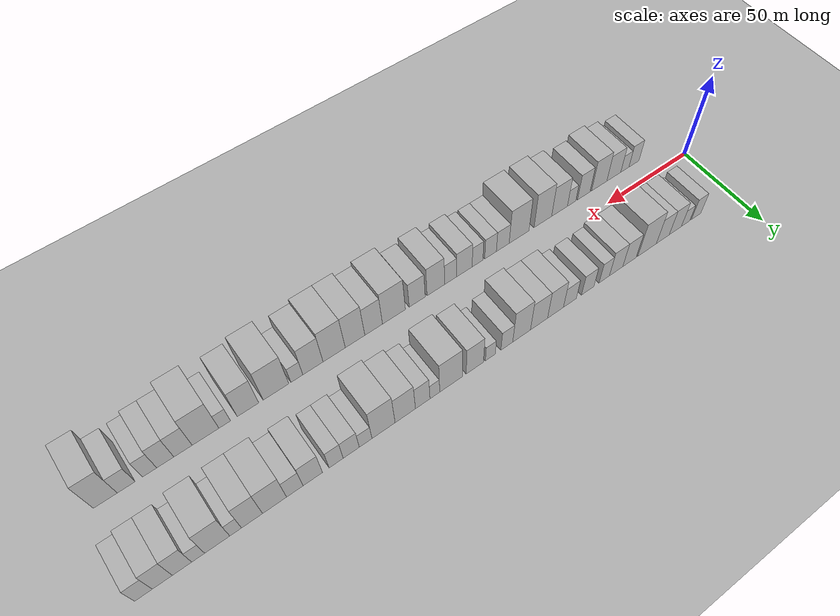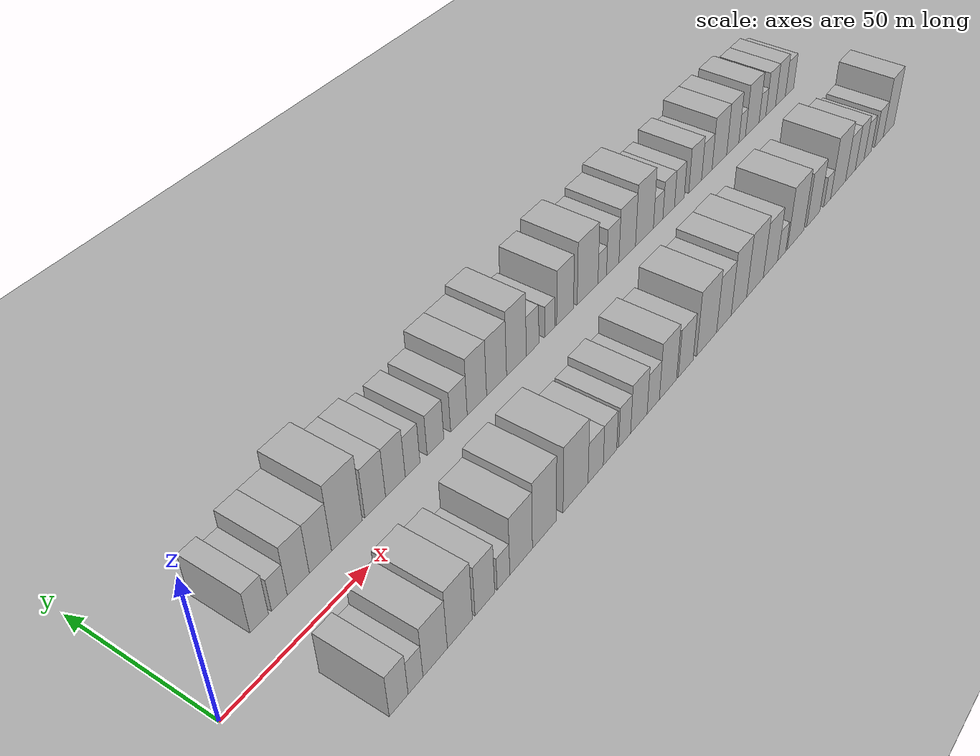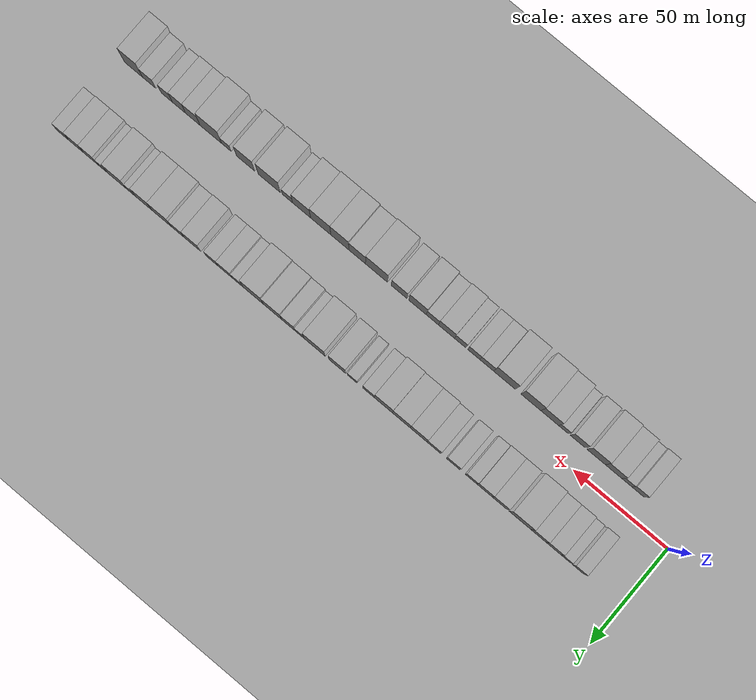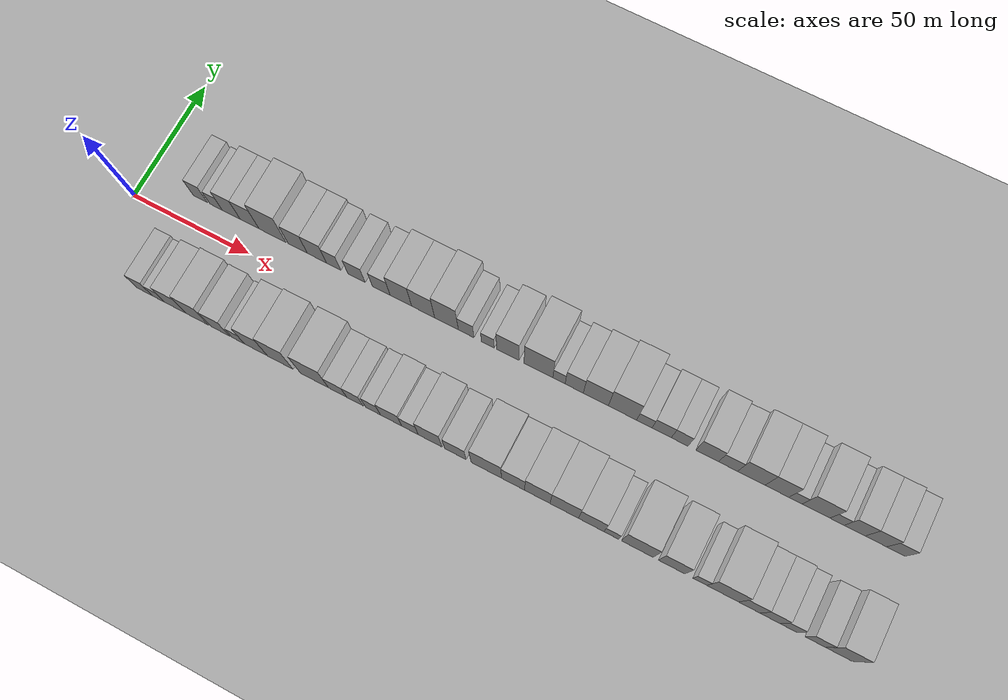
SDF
<?xml version="1.0" encoding="utf-8"?>

<sdf version="1.6">

   <world name="default">

      <gui fullscreen="0">

         <camera name="user_camera">

            <pose>-15 0 4.57585 0 0 0</pose>

            <view_controller>orbit</view_controller>

         </camera>

      </gui>

      <scene>

         <sky>

           <clouds>

             <speed>12</speed>

           </clouds>

         </sky>

         <ambient>0.4 0.4 0.4 1</ambient>

         <background>0.7 0.7 0.7 1</background>

         <shadows>1</shadows>

      </scene>

      <gravity>0 0 -9.8066</gravity>

      <magnetic_field>6e-06 2.3e-05 -4.2e-05</magnetic_field>

      <physics default="0" name="default_physics" type="ode">

         <ode>

            <solver>

               <type>quick</type>

               <iters>10</iters>

               <sor>1.0</sor>

               <use_dynamic_moi_rescaling>0</use_dynamic_moi_rescaling>

            </solver>

            <constraints>

               <cfm>0</cfm>

               <erp>0.2</erp>

               <contact_max_correcting_vel>100</contact_max_correcting_vel>

               <contact_surface_layer>0.001</contact_surface_layer>

            </constraints>

         </ode>

         <max_step_size>0.004</max_step_size>

         <real_time_factor>1</real_time_factor>

         <real_time_update_rate>250</real_time_update_rate>

      </physics>

      <light name="sun" type="directional">

         <cast_shadows>1</cast_shadows>

         <pose>0 0 10 0 0 0</pose>

         <diffuse>0.8 0.8 0.8 1</diffuse>

         <specular>0.2 0.2 0.2 1</specular>

         <attenuation>

            <range>1000</range>

            <constant>0.9</constant>

            <linear>0.01</linear>

            <quadratic>0.001</quadratic>

         </attenuation>

         <direction>-0.5 0.1 -0.9</direction>

      </light>

      <include>

         <name>ground_plane_1</name>

         <uri>model://HANNAS_ground_plane</uri>

         <pose>0 0 0  0 0 0</pose>

      </include>

      <include>

         <name>ground_plane_2</name>

         <uri>model://HANNAS_ground_plane</uri>

         <pose>100 0 0  0 0 0</pose>

      </include>

      <model name="building_1">

         <static>1</static>

         <pose frame="">23.0777 20.0000 0 0.000000 0.000000 1.570796</pose>

         <link name="link">

            <pose frame="">0 0 7.50 0 0 0</pose>

            <collision name="collision">

               <geometry>

                  <box>

                     <size>20.0000 6.1553 15.0000</size>

                  </box>

               </geometry>

               <max_contacts>10</max_contacts>

               <surface>

                  <contact>

                     <ode/>

                  </contact>

                  <bounce/>

                  <friction>

                     <torsional>

                        <ode/>

                     </torsional>

                     <ode/>

                  </friction>

               </surface>

            </collision>

            <visual name="visual">

               <cast_shadows>0</cast_shadows>

               <geometry>

                  <box>

                     <size>20.0000 6.1553 15.0000</size>

                  </box>

               </geometry>

               <material>

                  <script>

                     <uri>model://HANNAS_wall/materials/scripts</uri>

                     <uri>model://HANNAS_wall/materials/textures</uri>

                     <name>vrc/HANNAS_wall</name>

                  </script>

               </material>

            </visual>

            <self_collide>0</self_collide>

            <enable_wind>0</enable_wind>

            <kinematic>0</kinematic>

         </link>

      </model>

      <model name="building_2">

         <static>1</static>

         <pose frame="">29.8339 20.0000 0 0.000000 0.000000 1.570796</pose>

         <link name="link">

            <pose frame="">0 0 6.00 0 0 0</pose>

            <collision name="collision">

               <geometry>

                  <box>

                     <size>20.0000 5.3571 12.0000</size>

                  </box>

               </geometry>

               <max_contacts>10</max_contacts>

               <surface>

                  <contact>

                     <ode/>

                  </contact>

                  <bounce/>

                  <friction>

                     <torsional>

                        <ode/>

                     </torsional>

                     <ode/>

                  </friction>

               </surface>

            </collision>

            <visual name="visual">

               <cast_shadows>0</cast_shadows>

               <geometry>

                  <box>

                     <size>20.0000 5.3571 12.0000</size>

                  </box>

               </geometry>

               <material>

                  <script>

                     <uri>model://HANNAS_wall/materials/scripts</uri>

                     <uri>model://HANNAS_wall/materials/textures</uri>

                     <name>vrc/HANNAS_wall</name>

                  </script>

               </material>

            </visual>

            <self_collide>0</self_collide>

            <enable_wind>0</enable_wind>

            <kinematic>0</kinematic>

         </link>

      </model>

      <model name="building_3">

         <static>1</static>

         <pose frame="">36.3732 20.0000 0 0.000000 0.000000 1.570796</pose>

         <link name="link">

            <pose frame="">0 0 9.00 0 0 0</pose>

            <collision name="collision">

               <geometry>

                  <box>

                     <size>20.0000 7.7216 18.0000</size>

                  </box>

               </geometry>

               <max_contacts>10</max_contacts>

               <surface>

                  <contact>

                     <ode/>

                  </contact>

                  <bounce/>

                  <friction>

                     <torsional>

                        <ode/>

                     </torsional>

                     <ode/>

                  </friction>

               </surface>

            </collision>

            <visual name="visual">

               <cast_shadows>0</cast_shadows>

               <geometry>

                  <box>

                     <size>20.0000 7.7216 18.0000</size>

                  </box>

               </geometry>

               <material>

                  <script>

                     <uri>model://HANNAS_wall/materials/scripts</uri>

                     <uri>model://HANNAS_wall/materials/textures</uri>

                     <name>vrc/HANNAS_wall</name>

                  </script>

               </material>

            </visual>

            <self_collide>0</self_collide>

            <enable_wind>0</enable_wind>

            <kinematic>0</kinematic>

         </link>

      </model>

      <model name="building_4">

         <static>1</static>

         <pose frame="">44.2549 20.0000 0 0.000000 0.000000 1.570796</pose>

         <link name="link">

            <pose frame="">0 0 9.00 0 0 0</pose>

            <collision name="collision">

               <geometry>

                  <box>

                     <size>20.0000 8.0418 18.0000</size>

                  </box>

               </geometry>

               <max_contacts>10</max_contacts>

               <surface>

                  <contact>

                     <ode/>

                  </contact>

                  <bounce/>

                  <friction>

                     <torsional>

                        <ode/>

                     </torsional>

                     <ode/>

                  </friction>

               </surface>

            </collision>

            <visual name="visual">

               <cast_shadows>0</cast_shadows>

               <geometry>

                  <box>

                     <size>20.0000 8.0418 18.0000</size>

                  </box>

               </geometry>

               <material>

                  <script>

                     <uri>model://HANNAS_wall/materials/scripts</uri>

                     <uri>model://HANNAS_wall/materials/textures</uri>

                     <name>vrc/HANNAS_wall</name>

                  </script>

               </material>

            </visual>

            <self_collide>0</self_collide>

            <enable_wind>0</enable_wind>

            <kinematic>0</kinematic>

         </link>

      </model>

      <model name="building_5">

         <static>1</static>

         <pose frame="">54.0104 20.0000 0 0.000000 0.000000 1.570796</pose>

         <link name="link">

            <pose frame="">0 0 12.00 0 0 0</pose>

            <collision name="collision">

               <geometry>

                  <box>

                     <size>20.0000 11.4692 24.0000</size>

                  </box>

               </geometry>

               <max_contacts>10</max_contacts>

               <surface>

                  <contact>

                     <ode/>

                  </contact>

                  <bounce/>

                  <friction>

                     <torsional>

                        <ode/>

                     </torsional>

                     <ode/>

                  </friction>

               </surface>

            </collision>

            <visual name="visual">

               <cast_shadows>0</cast_shadows>

               <geometry>

                  <box>

                     <size>20.0000 11.4692 24.0000</size>

                  </box>

               </geometry>

               <material>

                  <script>

                     <uri>model://HANNAS_wall/materials/scripts</uri>

                     <uri>model://HANNAS_wall/materials/textures</uri>

                     <name>vrc/HANNAS_wall</name>

                  </script>

               </material>

            </visual>

            <self_collide>0</self_collide>

            <enable_wind>0</enable_wind>

            <kinematic>0</kinematic>

         </link>

      </model>

      <model name="building_6">

         <static>1</static>

         <pose frame="">64.8047 20.0000 0 0.000000 0.000000 1.570796</pose>

         <link name="link">

            <pose frame="">0 0 9.00 0 0 0</pose>

            <collision name="collision">

               <geometry>

                  <box>

                     <size>20.0000 8.1195 18.0000</size>

                  </box>

               </geometry>

               <max_contacts>10</max_contacts>

               <surface>

                  <contact>

                     <ode/>

                  </contact>

                  <bounce/>

                  <friction>

                     <torsional>

                        <ode/>

                     </torsional>

                     <ode/>

                  </friction>

               </surface>

            </collision>

            <visual name="visual">

               <cast_shadows>0</cast_shadows>

               <geometry>

                  <box>

                     <size>20.0000 8.1195 18.0000</size>

                  </box>

               </geometry>

               <material>

                  <script>

                     <uri>model://HANNAS_wall/materials/scripts</uri>

                     <uri>model://HANNAS_wall/materials/textures</uri>

                     <name>vrc/HANNAS_wall</name>

                  </script>

               </material>

            </visual>

            <self_collide>0</self_collide>

            <enable_wind>0</enable_wind>

            <kinematic>0</kinematic>

         </link>

      </model>

      <model name="building_7">

         <static>1</static>

         <pose frame="">72.8513 20.0000 0 0.000000 0.000000 1.570796</pose>

         <link name="link">

            <pose frame="">0 0 9.00 0 0 0</pose>

            <collision name="collision">

               <geometry>

                  <box>

                     <size>20.0000 7.9737 18.0000</size>

                  </box>

               </geometry>

               <max_contacts>10</max_contacts>

               <surface>

                  <contact>

                     <ode/>

                  </contact>

                  <bounce/>

                  <friction>

                     <torsional>

                        <ode/>

                     </torsional>

                     <ode/>

                  </friction>

               </surface>

            </collision>

            <visual name="visual">

               <cast_shadows>0</cast_shadows>

               <geometry>

                  <box>

                     <size>20.0000 7.9737 18.0000</size>

                  </box>

               </geometry>

               <material>

                  <script>

                     <uri>model://HANNAS_wall/materials/scripts</uri>

                     <uri>model://HANNAS_wall/materials/textures</uri>

                     <name>vrc/HANNAS_wall</name>

                  </script>

               </material>

            </visual>

            <self_collide>0</self_collide>

            <enable_wind>0</enable_wind>

            <kinematic>0</kinematic>

         </link>

      </model>

      <model name="building_8">

         <static>1</static>

         <pose frame="">79.8822 20.0000 0 0.000000 0.000000 1.570796</pose>

         <link name="link">

            <pose frame="">0 0 7.50 0 0 0</pose>

            <collision name="collision">

               <geometry>

                  <box>

                     <size>20.0000 6.0881 15.0000</size>

                  </box>

               </geometry>

               <max_contacts>10</max_contacts>

               <surface>

                  <contact>

                     <ode/>

                  </contact>

                  <bounce/>

                  <friction>

                     <torsional>

                        <ode/>

                     </torsional>

                     <ode/>

                  </friction>

               </surface>

            </collision>

            <visual name="visual">

               <cast_shadows>0</cast_shadows>

               <geometry>

                  <box>

                     <size>20.0000 6.0881 15.0000</size>

                  </box>

               </geometry>

               <material>

                  <script>

                     <uri>model://HANNAS_wall/materials/scripts</uri>

                     <uri>model://HANNAS_wall/materials/textures</uri>

                     <name>vrc/HANNAS_wall</name>

                  </script>

               </material>

            </visual>

            <self_collide>0</self_collide>

            <enable_wind>0</enable_wind>

            <kinematic>0</kinematic>

         </link>

      </model>

      <model name="building_9">

         <static>1</static>

         <pose frame="">89.5119 20.0000 0 0.000000 0.000000 1.570796</pose>

         <link name="link">

            <pose frame="">0 0 7.50 0 0 0</pose>

            <collision name="collision">

               <geometry>

                  <box>

                     <size>20.0000 7.1713 15.0000</size>

                  </box>

               </geometry>

               <max_contacts>10</max_contacts>

               <surface>

                  <contact>

                     <ode/>

                  </contact>

                  <bounce/>

                  <friction>

                     <torsional>

                        <ode/>

                     </torsional>

                     <ode/>

                  </friction>

               </surface>

            </collision>

            <visual name="visual">

               <cast_shadows>0</cast_shadows>

               <geometry>

                  <box>

                     <size>20.0000 7.1713 15.0000</size>

                  </box>

               </geometry>

               <material>

                  <script>

                     <uri>model://HANNAS_wall/materials/scripts</uri>

                     <uri>model://HANNAS_wall/materials/textures</uri>

                     <name>vrc/HANNAS_wall</name>

                  </script>

               </material>

            </visual>

            <self_collide>0</self_collide>

            <enable_wind>0</enable_wind>

            <kinematic>0</kinematic>

         </link>

      </model>

      <model name="building_10">

         <static>1</static>

         <pose frame="">99.7759 20.0000 0 0.000000 0.000000 1.570796</pose>

         <link name="link">

            <pose frame="">0 0 7.50 0 0 0</pose>

            <collision name="collision">

               <geometry>

                  <box>

                     <size>20.0000 7.3567 15.0000</size>

                  </box>

               </geometry>

               <max_contacts>10</max_contacts>

               <surface>

                  <contact>

                     <ode/>

                  </contact>

                  <bounce/>

                  <friction>

                     <torsional>

                        <ode/>

                     </torsional>

                     <ode/>

                  </friction>

               </surface>

            </collision>

            <visual name="visual">

               <cast_shadows>0</cast_shadows>

               <geometry>

                  <box>

                     <size>20.0000 7.3567 15.0000</size>

                  </box>

               </geometry>

               <material>

                  <script>

                     <uri>model://HANNAS_wall/materials/scripts</uri>

                     <uri>model://HANNAS_wall/materials/textures</uri>

                     <name>vrc/HANNAS_wall</name>

                  </script>

               </material>

            </visual>

            <self_collide>0</self_collide>

            <enable_wind>0</enable_wind>

            <kinematic>0</kinematic>

         </link>

      </model>

      <model name="building_11">

         <static>1</static>

         <pose frame="">107.9062 20.0000 0 0.000000 0.000000 1.570796</pose>

         <link name="link">

            <pose frame="">0 0 10.50 0 0 0</pose>

            <collision name="collision">

               <geometry>

                  <box>

                     <size>20.0000 8.9038 21.0000</size>

                  </box>

               </geometry>

               <max_contacts>10</max_contacts>

               <surface>

                  <contact>

                     <ode/>

                  </contact>

                  <bounce/>

                  <friction>

                     <torsional>

                        <ode/>

                     </torsional>

                     <ode/>

                  </friction>

               </surface>

            </collision>

            <visual name="visual">

               <cast_shadows>0</cast_shadows>

               <geometry>

                  <box>

                     <size>20.0000 8.9038 21.0000</size>

                  </box>

               </geometry>

               <material>

                  <script>

                     <uri>model://HANNAS_wall/materials/scripts</uri>

                     <uri>model://HANNAS_wall/materials/textures</uri>

                     <name>vrc/HANNAS_wall</name>

                  </script>

               </material>

            </visual>

            <self_collide>0</self_collide>

            <enable_wind>0</enable_wind>

            <kinematic>0</kinematic>

         </link>

      </model>

      <model name="building_12">

         <static>1</static>

         <pose frame="">117.0922 20.0000 0 0.000000 0.000000 1.570796</pose>

         <link name="link">

            <pose frame="">0 0 10.50 0 0 0</pose>

            <collision name="collision">

               <geometry>

                  <box>

                     <size>20.0000 9.4683 21.0000</size>

                  </box>

               </geometry>

               <max_contacts>10</max_contacts>

               <surface>

                  <contact>

                     <ode/>

                  </contact>

                  <bounce/>

                  <friction>

                     <torsional>

                        <ode/>

                     </torsional>

                     <ode/>

                  </friction>

               </surface>

            </collision>

            <visual name="visual">

               <cast_shadows>0</cast_shadows>

               <geometry>

                  <box>

                     <size>20.0000 9.4683 21.0000</size>

                  </box>

               </geometry>

               <material>

                  <script>

                     <uri>model://HANNAS_wall/materials/scripts</uri>

                     <uri>model://HANNAS_wall/materials/textures</uri>

                     <name>vrc/HANNAS_wall</name>

                  </script>

               </material>

            </visual>

            <self_collide>0</self_collide>

            <enable_wind>0</enable_wind>

            <kinematic>0</kinematic>

         </link>

      </model>

      <model name="building_13">

         <static>1</static>

         <pose frame="">126.6533 20.0000 0 0.000000 0.000000 1.570796</pose>

         <link name="link">

            <pose frame="">0 0 12.00 0 0 0</pose>

            <collision name="collision">

               <geometry>

                  <box>

                     <size>20.0000 9.6539 24.0000</size>

                  </box>

               </geometry>

               <max_contacts>10</max_contacts>

               <surface>

                  <contact>

                     <ode/>

                  </contact>

                  <bounce/>

                  <friction>

                     <torsional>

                        <ode/>

                     </torsional>

                     <ode/>

                  </friction>

               </surface>

            </collision>

            <visual name="visual">

               <cast_shadows>0</cast_shadows>

               <geometry>

                  <box>

                     <size>20.0000 9.6539 24.0000</size>

                  </box>

               </geometry>

               <material>

                  <script>

                     <uri>model://HANNAS_wall/materials/scripts</uri>

                     <uri>model://HANNAS_wall/materials/textures</uri>

                     <name>vrc/HANNAS_wall</name>

                  </script>

               </material>

            </visual>

            <self_collide>0</self_collide>

            <enable_wind>0</enable_wind>

            <kinematic>0</kinematic>

         </link>

      </model>

      <model name="building_14">

         <static>1</static>

         <pose frame="">134.6516 20.0000 0 0.000000 0.000000 1.570796</pose>

         <link name="link">

            <pose frame="">0 0 7.50 0 0 0</pose>

            <collision name="collision">

               <geometry>

                  <box>

                     <size>20.0000 6.3426 15.0000</size>

                  </box>

               </geometry>

               <max_contacts>10</max_contacts>

               <surface>

                  <contact>

                     <ode/>

                  </contact>

                  <bounce/>

                  <friction>

                     <torsional>

                        <ode/>

                     </torsional>

                     <ode/>

                  </friction>

               </surface>

            </collision>

            <visual name="visual">

               <cast_shadows>0</cast_shadows>

               <geometry>

                  <box>

                     <size>20.0000 6.3426 15.0000</size>

                  </box>

               </geometry>

               <material>

                  <script>

                     <uri>model://HANNAS_wall/materials/scripts</uri>

                     <uri>model://HANNAS_wall/materials/textures</uri>

                     <name>vrc/HANNAS_wall</name>

                  </script>

               </material>

            </visual>

            <self_collide>0</self_collide>

            <enable_wind>0</enable_wind>

            <kinematic>0</kinematic>

         </link>

      </model>

      <model name="building_15">

         <static>1</static>

         <pose frame="">143.4204 20.0000 0 0.000000 0.000000 1.570796</pose>

         <link name="link">

            <pose frame="">0 0 6.00 0 0 0</pose>

            <collision name="collision">

               <geometry>

                  <box>

                     <size>20.0000 5.1950 12.0000</size>

                  </box>

               </geometry>

               <max_contacts>10</max_contacts>

               <surface>

                  <contact>

                     <ode/>

                  </contact>

                  <bounce/>

                  <friction>

                     <torsional>

                        <ode/>

                     </torsional>

                     <ode/>

                  </friction>

               </surface>

            </collision>

            <visual name="visual">

               <cast_shadows>0</cast_shadows>

               <geometry>

                  <box>

                     <size>20.0000 5.1950 12.0000</size>

                  </box>

               </geometry>

               <material>

                  <script>

                     <uri>model://HANNAS_wall/materials/scripts</uri>

                     <uri>model://HANNAS_wall/materials/textures</uri>

                     <name>vrc/HANNAS_wall</name>

                  </script>

               </material>

            </visual>

            <self_collide>0</self_collide>

            <enable_wind>0</enable_wind>

            <kinematic>0</kinematic>

         </link>

      </model>

      <model name="building_16">

         <static>1</static>

         <pose frame="">151.5093 20.0000 0 0.000000 0.000000 1.570796</pose>

         <link name="link">

            <pose frame="">0 0 10.50 0 0 0</pose>

            <collision name="collision">

               <geometry>

                  <box>

                     <size>20.0000 8.9827 21.0000</size>

                  </box>

               </geometry>

               <max_contacts>10</max_contacts>

               <surface>

                  <contact>

                     <ode/>

                  </contact>

                  <bounce/>

                  <friction>

                     <torsional>

                        <ode/>

                     </torsional>

                     <ode/>

                  </friction>

               </surface>

            </collision>

            <visual name="visual">

               <cast_shadows>0</cast_shadows>

               <geometry>

                  <box>

                     <size>20.0000 8.9827 21.0000</size>

                  </box>

               </geometry>

               <material>

                  <script>

                     <uri>model://HANNAS_wall/materials/scripts</uri>

                     <uri>model://HANNAS_wall/materials/textures</uri>

                     <name>vrc/HANNAS_wall</name>

                  </script>

               </material>

            </visual>

            <self_collide>0</self_collide>

            <enable_wind>0</enable_wind>

            <kinematic>0</kinematic>

         </link>

      </model>

      <model name="building_17">

         <static>1</static>

         <pose frame="">163.7440 20.0000 0 0.000000 0.000000 1.570796</pose>

         <link name="link">

            <pose frame="">0 0 12.00 0 0 0</pose>

            <collision name="collision">

               <geometry>

                  <box>

                     <size>20.0000 11.4867 24.0000</size>

                  </box>

               </geometry>

               <max_contacts>10</max_contacts>

               <surface>

                  <contact>

                     <ode/>

                  </contact>

                  <bounce/>

                  <friction>

                     <torsional>

                        <ode/>

                     </torsional>

                     <ode/>

                  </friction>

               </surface>

            </collision>

            <visual name="visual">

               <cast_shadows>0</cast_shadows>

               <geometry>

                  <box>

                     <size>20.0000 11.4867 24.0000</size>

                  </box>

               </geometry>

               <material>

                  <script>

                     <uri>model://HANNAS_wall/materials/scripts</uri>

                     <uri>model://HANNAS_wall/materials/textures</uri>

                     <name>vrc/HANNAS_wall</name>

                  </script>

               </material>

            </visual>

            <self_collide>0</self_collide>

            <enable_wind>0</enable_wind>

            <kinematic>0</kinematic>

         </link>

      </model>

      <model name="building_18">

         <static>1</static>

         <pose frame="">171.9253 20.0000 0 0.000000 0.000000 1.570796</pose>

         <link name="link">

            <pose frame="">0 0 6.00 0 0 0</pose>

            <collision name="collision">

               <geometry>

                  <box>

                     <size>20.0000 4.8759 12.0000</size>

                  </box>

               </geometry>

               <max_contacts>10</max_contacts>

               <surface>

                  <contact>

                     <ode/>

                  </contact>

                  <bounce/>

                  <friction>

                     <torsional>

                        <ode/>

                     </torsional>

                     <ode/>

                  </friction>

               </surface>

            </collision>

            <visual name="visual">

               <cast_shadows>0</cast_shadows>

               <geometry>

                  <box>

                     <size>20.0000 4.8759 12.0000</size>

                  </box>

               </geometry>

               <material>

                  <script>

                     <uri>model://HANNAS_wall/materials/scripts</uri>

                     <uri>model://HANNAS_wall/materials/textures</uri>

                     <name>vrc/HANNAS_wall</name>

                  </script>

               </material>

            </visual>

            <self_collide>0</self_collide>

            <enable_wind>0</enable_wind>

            <kinematic>0</kinematic>

         </link>

      </model>

      <model name="building_19">

         <static>1</static>

         <pose frame="">177.9646 20.0000 0 0.000000 0.000000 1.570796</pose>

         <link name="link">

            <pose frame="">0 0 9.00 0 0 0</pose>

            <collision name="collision">

               <geometry>

                  <box>

                     <size>20.0000 7.2027 18.0000</size>

                  </box>

               </geometry>

               <max_contacts>10</max_contacts>

               <surface>

                  <contact>

                     <ode/>

                  </contact>

                  <bounce/>

                  <friction>

                     <torsional>

                        <ode/>

                     </torsional>

                     <ode/>

                  </friction>

               </surface>

            </collision>

            <visual name="visual">

               <cast_shadows>0</cast_shadows>

               <geometry>

                  <box>

                     <size>20.0000 7.2027 18.0000</size>

                  </box>

               </geometry>

               <material>

                  <script>

                     <uri>model://HANNAS_wall/materials/scripts</uri>

                     <uri>model://HANNAS_wall/materials/textures</uri>

                     <name>vrc/HANNAS_wall</name>

                  </script>

               </material>

            </visual>

            <self_collide>0</self_collide>

            <enable_wind>0</enable_wind>

            <kinematic>0</kinematic>

         </link>

      </model>

      <model name="building_20">

         <static>1</static>

         <pose frame="">186.5161 20.0000 0 0.000000 0.000000 1.570796</pose>

         <link name="link">

            <pose frame="">0 0 10.50 0 0 0</pose>

            <collision name="collision">

               <geometry>

                  <box>

                     <size>20.0000 9.9005 21.0000</size>

                  </box>

               </geometry>

               <max_contacts>10</max_contacts>

               <surface>

                  <contact>

                     <ode/>

                  </contact>

                  <bounce/>

                  <friction>

                     <torsional>

                        <ode/>

                     </torsional>

                     <ode/>

                  </friction>

               </surface>

            </collision>

            <visual name="visual">

               <cast_shadows>0</cast_shadows>

               <geometry>

                  <box>

                     <size>20.0000 9.9005 21.0000</size>

                  </box>

               </geometry>

               <material>

                  <script>

                     <uri>model://HANNAS_wall/materials/scripts</uri>

                     <uri>model://HANNAS_wall/materials/textures</uri>

                     <name>vrc/HANNAS_wall</name>

                  </script>

               </material>

            </visual>

            <self_collide>0</self_collide>

            <enable_wind>0</enable_wind>

            <kinematic>0</kinematic>

         </link>

      </model>

      <model name="building_21">

         <static>1</static>

         <pose frame="">196.9887 20.0000 0 0.000000 0.000000 1.570796</pose>

         <link name="link">

            <pose frame="">0 0 12.00 0 0 0</pose>

            <collision name="collision">

               <geometry>

                  <box>

                     <size>20.0000 11.0446 24.0000</size>

                  </box>

               </geometry>

               <max_contacts>10</max_contacts>

               <surface>

                  <contact>

                     <ode/>

                  </contact>

                  <bounce/>

                  <friction>

                     <torsional>

                        <ode/>

                     </torsional>

                     <ode/>

                  </friction>

               </surface>

            </collision>

            <visual name="visual">

               <cast_shadows>0</cast_shadows>

               <geometry>

                  <box>

                     <size>20.0000 11.0446 24.0000</size>

                  </box>

               </geometry>

               <material>

                  <script>

                     <uri>model://HANNAS_wall/materials/scripts</uri>

                     <uri>model://HANNAS_wall/materials/textures</uri>

                     <name>vrc/HANNAS_wall</name>

                  </script>

               </material>

            </visual>

            <self_collide>0</self_collide>

            <enable_wind>0</enable_wind>

            <kinematic>0</kinematic>

         </link>

      </model>

      <model name="building_22">

         <static>1</static>

         <pose frame="">205.5087 20.0000 0 0.000000 0.000000 1.570796</pose>

         <link name="link">

            <pose frame="">0 0 6.00 0 0 0</pose>

            <collision name="collision">

               <geometry>

                  <box>

                     <size>20.0000 5.9953 12.0000</size>

                  </box>

               </geometry>

               <max_contacts>10</max_contacts>

               <surface>

                  <contact>

                     <ode/>

                  </contact>

                  <bounce/>

                  <friction>

                     <torsional>

                        <ode/>

                     </torsional>

                     <ode/>

                  </friction>

               </surface>

            </collision>

            <visual name="visual">

               <cast_shadows>0</cast_shadows>

               <geometry>

                  <box>

                     <size>20.0000 5.9953 12.0000</size>

                  </box>

               </geometry>

               <material>

                  <script>

                     <uri>model://HANNAS_wall/materials/scripts</uri>

                     <uri>model://HANNAS_wall/materials/textures</uri>

                     <name>vrc/HANNAS_wall</name>

                  </script>

               </material>

            </visual>

            <self_collide>0</self_collide>

            <enable_wind>0</enable_wind>

            <kinematic>0</kinematic>

         </link>

      </model>

      <model name="building_23">

         <static>1</static>

         <pose frame="">212.2423 20.0000 0 0.000000 0.000000 1.570796</pose>

         <link name="link">

            <pose frame="">0 0 7.50 0 0 0</pose>

            <collision name="collision">

               <geometry>

                  <box>

                     <size>20.0000 7.4719 15.0000</size>

                  </box>

               </geometry>

               <max_contacts>10</max_contacts>

               <surface>

                  <contact>

                     <ode/>

                  </contact>

                  <bounce/>

                  <friction>

                     <torsional>

                        <ode/>

                     </torsional>

                     <ode/>

                  </friction>

               </surface>

            </collision>

            <visual name="visual">

               <cast_shadows>0</cast_shadows>

               <geometry>

                  <box>

                     <size>20.0000 7.4719 15.0000</size>

                  </box>

               </geometry>

               <material>

                  <script>

                     <uri>model://HANNAS_wall/materials/scripts</uri>

                     <uri>model://HANNAS_wall/materials/textures</uri>

                     <name>vrc/HANNAS_wall</name>

                  </script>

               </material>

            </visual>

            <self_collide>0</self_collide>

            <enable_wind>0</enable_wind>

            <kinematic>0</kinematic>

         </link>

      </model>

      <model name="building_24">

         <static>1</static>

         <pose frame="">219.1995 20.0000 0 0.000000 0.000000 1.570796</pose>

         <link name="link">

            <pose frame="">0 0 7.50 0 0 0</pose>

            <collision name="collision">

               <geometry>

                  <box>

                     <size>20.0000 6.4427 15.0000</size>

                  </box>

               </geometry>

               <max_contacts>10</max_contacts>

               <surface>

                  <contact>

                     <ode/>

                  </contact>

                  <bounce/>

                  <friction>

                     <torsional>

                        <ode/>

                     </torsional>

                     <ode/>

                  </friction>

               </surface>

            </collision>

            <visual name="visual">

               <cast_shadows>0</cast_shadows>

               <geometry>

                  <box>

                     <size>20.0000 6.4427 15.0000</size>

                  </box>

               </geometry>

               <material>

                  <script>

                     <uri>model://HANNAS_wall/materials/scripts</uri>

                     <uri>model://HANNAS_wall/materials/textures</uri>

                     <name>vrc/HANNAS_wall</name>

                  </script>

               </material>

            </visual>

            <self_collide>0</self_collide>

            <enable_wind>0</enable_wind>

            <kinematic>0</kinematic>

         </link>

      </model>

      <model name="building_25">

         <static>1</static>

         <pose frame="">229.7864 20.0000 0 0.000000 0.000000 1.570796</pose>

         <link name="link">

            <pose frame="">0 0 9.00 0 0 0</pose>

            <collision name="collision">

               <geometry>

                  <box>

                     <size>20.0000 8.7310 18.0000</size>

                  </box>

               </geometry>

               <max_contacts>10</max_contacts>

               <surface>

                  <contact>

                     <ode/>

                  </contact>

                  <bounce/>

                  <friction>

                     <torsional>

                        <ode/>

                     </torsional>

                     <ode/>

                  </friction>

               </surface>

            </collision>

            <visual name="visual">

               <cast_shadows>0</cast_shadows>

               <geometry>

                  <box>

                     <size>20.0000 8.7310 18.0000</size>

                  </box>

               </geometry>

               <material>

                  <script>

                     <uri>model://HANNAS_wall/materials/scripts</uri>

                     <uri>model://HANNAS_wall/materials/textures</uri>

                     <name>vrc/HANNAS_wall</name>

                  </script>

               </material>

            </visual>

            <self_collide>0</self_collide>

            <enable_wind>0</enable_wind>

            <kinematic>0</kinematic>

         </link>

      </model>

      <model name="building_26">

         <static>1</static>

         <pose frame="">237.7933 20.0000 0 0.000000 0.000000 1.570796</pose>

         <link name="link">

            <pose frame="">0 0 7.50 0 0 0</pose>

            <collision name="collision">

               <geometry>

                  <box>

                     <size>20.0000 7.2829 15.0000</size>

                  </box>

               </geometry>

               <max_contacts>10</max_contacts>

               <surface>

                  <contact>

                     <ode/>

                  </contact>

                  <bounce/>

                  <friction>

                     <torsional>

                        <ode/>

                     </torsional>

                     <ode/>

                  </friction>

               </surface>

            </collision>

            <visual name="visual">

               <cast_shadows>0</cast_shadows>

               <geometry>

                  <box>

                     <size>20.0000 7.2829 15.0000</size>

                  </box>

               </geometry>

               <material>

                  <script>

                     <uri>model://HANNAS_wall/materials/scripts</uri>

                     <uri>model://HANNAS_wall/materials/textures</uri>

                     <name>vrc/HANNAS_wall</name>

                  </script>

               </material>

            </visual>

            <self_collide>0</self_collide>

            <enable_wind>0</enable_wind>

            <kinematic>0</kinematic>

         </link>

      </model>

      <model name="building_27">

         <static>1</static>

         <pose frame="">246.6524 20.0000 0 0.000000 0.000000 1.570796</pose>

         <link name="link">

            <pose frame="">0 0 10.50 0 0 0</pose>

            <collision name="collision">

               <geometry>

                  <box>

                     <size>20.0000 10.4353 21.0000</size>

                  </box>

               </geometry>

               <max_contacts>10</max_contacts>

               <surface>

                  <contact>

                     <ode/>

                  </contact>

                  <bounce/>

                  <friction>

                     <torsional>

                        <ode/>

                     </torsional>

                     <ode/>

                  </friction>

               </surface>

            </collision>

            <visual name="visual">

               <cast_shadows>0</cast_shadows>

               <geometry>

                  <box>

                     <size>20.0000 10.4353 21.0000</size>

                  </box>

               </geometry>

               <material>

                  <script>

                     <uri>model://HANNAS_wall/materials/scripts</uri>

                     <uri>model://HANNAS_wall/materials/textures</uri>

                     <name>vrc/HANNAS_wall</name>

                  </script>

               </material>

            </visual>

            <self_collide>0</self_collide>

            <enable_wind>0</enable_wind>

            <kinematic>0</kinematic>

         </link>

      </model>

      <model name="building_28">

         <static>1</static>

         <pose frame="">256.3481 20.0000 0 0.000000 0.000000 1.570796</pose>

         <link name="link">

            <pose frame="">0 0 10.50 0 0 0</pose>

            <collision name="collision">

               <geometry>

                  <box>

                     <size>20.0000 8.9560 21.0000</size>

                  </box>

               </geometry>

               <max_contacts>10</max_contacts>

               <surface>

                  <contact>

                     <ode/>

                  </contact>

                  <bounce/>

                  <friction>

                     <torsional>

                        <ode/>

                     </torsional>

                     <ode/>

                  </friction>

               </surface>

            </collision>

            <visual name="visual">

               <cast_shadows>0</cast_shadows>

               <geometry>

                  <box>

                     <size>20.0000 8.9560 21.0000</size>

                  </box>

               </geometry>

               <material>

                  <script>

                     <uri>model://HANNAS_wall/materials/scripts</uri>

                     <uri>model://HANNAS_wall/materials/textures</uri>

                     <name>vrc/HANNAS_wall</name>

                  </script>

               </material>

            </visual>

            <self_collide>0</self_collide>

            <enable_wind>0</enable_wind>

            <kinematic>0</kinematic>

         </link>

      </model>

      <model name="building_29">

         <static>1</static>

         <pose frame="">263.2958 20.0000 0 0.000000 0.000000 1.570796</pose>

         <link name="link">

            <pose frame="">0 0 6.00 0 0 0</pose>

            <collision name="collision">

               <geometry>

                  <box>

                     <size>20.0000 4.9395 12.0000</size>

                  </box>

               </geometry>

               <max_contacts>10</max_contacts>

               <surface>

                  <contact>

                     <ode/>

                  </contact>

                  <bounce/>

                  <friction>

                     <torsional>

                        <ode/>

                     </torsional>

                     <ode/>

                  </friction>

               </surface>

            </collision>

            <visual name="visual">

               <cast_shadows>0</cast_shadows>

               <geometry>

                  <box>

                     <size>20.0000 4.9395 12.0000</size>

                  </box>

               </geometry>

               <material>

                  <script>

                     <uri>model://HANNAS_wall/materials/scripts</uri>

                     <uri>model://HANNAS_wall/materials/textures</uri>

                     <name>vrc/HANNAS_wall</name>

                  </script>

               </material>

            </visual>

            <self_collide>0</self_collide>

            <enable_wind>0</enable_wind>

            <kinematic>0</kinematic>

         </link>

      </model>

      <model name="building_30">

         <static>1</static>

         <pose frame="">270.9607 20.0000 0 0.000000 0.000000 1.570796</pose>

         <link name="link">

            <pose frame="">0 0 10.50 0 0 0</pose>

            <collision name="collision">

               <geometry>

                  <box>

                     <size>20.0000 10.3903 21.0000</size>

                  </box>

               </geometry>

               <max_contacts>10</max_contacts>

               <surface>

                  <contact>

                     <ode/>

                  </contact>

                  <bounce/>

                  <friction>

                     <torsional>

                        <ode/>

                     </torsional>

                     <ode/>

                  </friction>

               </surface>

            </collision>

            <visual name="visual">

               <cast_shadows>0</cast_shadows>

               <geometry>

                  <box>

                     <size>20.0000 10.3903 21.0000</size>

                  </box>

               </geometry>

               <material>

                  <script>

                     <uri>model://HANNAS_wall/materials/scripts</uri>

                     <uri>model://HANNAS_wall/materials/textures</uri>

                     <name>vrc/HANNAS_wall</name>

                  </script>

               </material>

            </visual>

            <self_collide>0</self_collide>

            <enable_wind>0</enable_wind>

            <kinematic>0</kinematic>

         </link>

      </model>

      <model name="building_31">

         <static>1</static>

         <pose frame="">278.8048 20.0000 0 0.000000 0.000000 1.570796</pose>

         <link name="link">

            <pose frame="">0 0 6.00 0 0 0</pose>

            <collision name="collision">

               <geometry>

                  <box>

                     <size>20.0000 5.2979 12.0000</size>

                  </box>

               </geometry>

               <max_contacts>10</max_contacts>

               <surface>

                  <contact>

                     <ode/>

                  </contact>

                  <bounce/>

                  <friction>

                     <torsional>

                        <ode/>

                     </torsional>

                     <ode/>

                  </friction>

               </surface>

            </collision>

            <visual name="visual">

               <cast_shadows>0</cast_shadows>

               <geometry>

                  <box>

                     <size>20.0000 5.2979 12.0000</size>

                  </box>

               </geometry>

               <material>

                  <script>

                     <uri>model://HANNAS_wall/materials/scripts</uri>

                     <uri>model://HANNAS_wall/materials/textures</uri>

                     <name>vrc/HANNAS_wall</name>

                  </script>

               </material>

            </visual>

            <self_collide>0</self_collide>

            <enable_wind>0</enable_wind>

            <kinematic>0</kinematic>

         </link>

      </model>

      <model name="building_32">

         <static>1</static>

         <pose frame="">285.3369 20.0000 0 0.000000 0.000000 1.570796</pose>

         <link name="link">

            <pose frame="">0 0 9.00 0 0 0</pose>

            <collision name="collision">

               <geometry>

                  <box>

                     <size>20.0000 7.7664 18.0000</size>

                  </box>

               </geometry>

               <max_contacts>10</max_contacts>

               <surface>

                  <contact>

                     <ode/>

                  </contact>

                  <bounce/>

                  <friction>

                     <torsional>

                        <ode/>

                     </torsional>

                     <ode/>

                  </friction>

               </surface>

            </collision>

            <visual name="visual">

               <cast_shadows>0</cast_shadows>

               <geometry>

                  <box>

                     <size>20.0000 7.7664 18.0000</size>

                  </box>

               </geometry>

               <material>

                  <script>

                     <uri>model://HANNAS_wall/materials/scripts</uri>

                     <uri>model://HANNAS_wall/materials/textures</uri>

                     <name>vrc/HANNAS_wall</name>

                  </script>

               </material>

            </visual>

            <self_collide>0</self_collide>

            <enable_wind>0</enable_wind>

            <kinematic>0</kinematic>

         </link>

      </model>

      <model name="building_33">

         <static>1</static>

         <pose frame="">293.1914 20.0000 0 0.000000 0.000000 1.570796</pose>

         <link name="link">

            <pose frame="">0 0 9.00 0 0 0</pose>

            <collision name="collision">

               <geometry>

                  <box>

                     <size>20.0000 7.9426 18.0000</size>

                  </box>

               </geometry>

               <max_contacts>10</max_contacts>

               <surface>

                  <contact>

                     <ode/>

                  </contact>

                  <bounce/>

                  <friction>

                     <torsional>

                        <ode/>

                     </torsional>

                     <ode/>

                  </friction>

               </surface>

            </collision>

            <visual name="visual">

               <cast_shadows>0</cast_shadows>

               <geometry>

                  <box>

                     <size>20.0000 7.9426 18.0000</size>

                  </box>

               </geometry>

               <material>

                  <script>

                     <uri>model://HANNAS_wall/materials/scripts</uri>

                     <uri>model://HANNAS_wall/materials/textures</uri>

                     <name>vrc/HANNAS_wall</name>

                  </script>

               </material>

            </visual>

            <self_collide>0</self_collide>

            <enable_wind>0</enable_wind>

            <kinematic>0</kinematic>

         </link>

      </model>

      <model name="building_34">

         <static>1</static>

         <pose frame="">300.5846 20.0000 0 0.000000 0.000000 1.570796</pose>

         <link name="link">

            <pose frame="">0 0 7.50 0 0 0</pose>

            <collision name="collision">

               <geometry>

                  <box>

                     <size>20.0000 6.8439 15.0000</size>

                  </box>

               </geometry>

               <max_contacts>10</max_contacts>

               <surface>

                  <contact>

                     <ode/>

                  </contact>

                  <bounce/>

                  <friction>

                     <torsional>

                        <ode/>

                     </torsional>

                     <ode/>

                  </friction>

               </surface>

            </collision>

            <visual name="visual">

               <cast_shadows>0</cast_shadows>

               <geometry>

                  <box>

                     <size>20.0000 6.8439 15.0000</size>

                  </box>

               </geometry>

               <material>

                  <script>

                     <uri>model://HANNAS_wall/materials/scripts</uri>

                     <uri>model://HANNAS_wall/materials/textures</uri>

                     <name>vrc/HANNAS_wall</name>

                  </script>

               </material>

            </visual>

            <self_collide>0</self_collide>

            <enable_wind>0</enable_wind>

            <kinematic>0</kinematic>

         </link>

      </model>

      <model name="building_35">

         <static>1</static>

         <pose frame="">24.2903 -20.0000 0 0.000000 0.000000 1.570796</pose>

         <link name="link">

            <pose frame="">0 0 7.50 0 0 0</pose>

            <collision name="collision">

               <geometry>

                  <box>

                     <size>20.0000 6.5806 15.0000</size>

                  </box>

               </geometry>

               <max_contacts>10</max_contacts>

               <surface>

                  <contact>

                     <ode/>

                  </contact>

                  <bounce/>

                  <friction>

                     <torsional>

                        <ode/>

                     </torsional>

                     <ode/>

                  </friction>

               </surface>

            </collision>

            <visual name="visual">

               <cast_shadows>0</cast_shadows>

               <geometry>

                  <box>

                     <size>20.0000 6.5806 15.0000</size>

                  </box>

               </geometry>

               <material>

                  <script>

                     <uri>model://HANNAS_wall/materials/scripts</uri>

                     <uri>model://HANNAS_wall/materials/textures</uri>

                     <name>vrc/HANNAS_wall</name>

                  </script>

               </material>

            </visual>

            <self_collide>0</self_collide>

            <enable_wind>0</enable_wind>

            <kinematic>0</kinematic>

         </link>

      </model>

      <model name="building_36">

         <static>1</static>

         <pose frame="">30.2217 -20.0000 0 0.000000 0.000000 1.570796</pose>

         <link name="link">

            <pose frame="">0 0 6.00 0 0 0</pose>

            <collision name="collision">

               <geometry>

                  <box>

                     <size>20.0000 5.2823 12.0000</size>

                  </box>

               </geometry>

               <max_contacts>10</max_contacts>

               <surface>

                  <contact>

                     <ode/>

                  </contact>

                  <bounce/>

                  <friction>

                     <torsional>

                        <ode/>

                     </torsional>

                     <ode/>

                  </friction>

               </surface>

            </collision>

            <visual name="visual">

               <cast_shadows>0</cast_shadows>

               <geometry>

                  <box>

                     <size>20.0000 5.2823 12.0000</size>

                  </box>

               </geometry>

               <material>

                  <script>

                     <uri>model://HANNAS_wall/materials/scripts</uri>

                     <uri>model://HANNAS_wall/materials/textures</uri>

                     <name>vrc/HANNAS_wall</name>

                  </script>

               </material>

            </visual>

            <self_collide>0</self_collide>

            <enable_wind>0</enable_wind>

            <kinematic>0</kinematic>

         </link>

      </model>

      <model name="building_37">

         <static>1</static>

         <pose frame="">37.3337 -20.0000 0 0.000000 0.000000 1.570796</pose>

         <link name="link">

            <pose frame="">0 0 9.00 0 0 0</pose>

            <collision name="collision">

               <geometry>

                  <box>

                     <size>20.0000 8.9416 18.0000</size>

                  </box>

               </geometry>

               <max_contacts>10</max_contacts>

               <surface>

                  <contact>

                     <ode/>

                  </contact>

                  <bounce/>

                  <friction>

                     <torsional>

                        <ode/>

                     </torsional>

                     <ode/>

                  </friction>

               </surface>

            </collision>

            <visual name="visual">

               <cast_shadows>0</cast_shadows>

               <geometry>

                  <box>

                     <size>20.0000 8.9416 18.0000</size>

                  </box>

               </geometry>

               <material>

                  <script>

                     <uri>model://HANNAS_wall/materials/scripts</uri>

                     <uri>model://HANNAS_wall/materials/textures</uri>

                     <name>vrc/HANNAS_wall</name>

                  </script>

               </material>

            </visual>

            <self_collide>0</self_collide>

            <enable_wind>0</enable_wind>

            <kinematic>0</kinematic>

         </link>

      </model>

      <model name="building_38">

         <static>1</static>

         <pose frame="">46.5936 -20.0000 0 0.000000 0.000000 1.570796</pose>

         <link name="link">

            <pose frame="">0 0 10.50 0 0 0</pose>

            <collision name="collision">

               <geometry>

                  <box>

                     <size>20.0000 9.5782 21.0000</size>

                  </box>

               </geometry>

               <max_contacts>10</max_contacts>

               <surface>

                  <contact>

                     <ode/>

                  </contact>

                  <bounce/>

                  <friction>

                     <torsional>

                        <ode/>

                     </torsional>

                     <ode/>

                  </friction>

               </surface>

            </collision>

            <visual name="visual">

               <cast_shadows>0</cast_shadows>

               <geometry>

                  <box>

                     <size>20.0000 9.5782 21.0000</size>

                  </box>

               </geometry>

               <material>

                  <script>

                     <uri>model://HANNAS_wall/materials/scripts</uri>

                     <uri>model://HANNAS_wall/materials/textures</uri>

                     <name>vrc/HANNAS_wall</name>

                  </script>

               </material>

            </visual>

            <self_collide>0</self_collide>

            <enable_wind>0</enable_wind>

            <kinematic>0</kinematic>

         </link>

      </model>

      <model name="building_39">

         <static>1</static>

         <pose frame="">56.2908 -20.0000 0 0.000000 0.000000 1.570796</pose>

         <link name="link">

            <pose frame="">0 0 9.00 0 0 0</pose>

            <collision name="collision">

               <geometry>

                  <box>

                     <size>20.0000 7.8160 18.0000</size>

                  </box>

               </geometry>

               <max_contacts>10</max_contacts>

               <surface>

                  <contact>

                     <ode/>

                  </contact>

                  <bounce/>

                  <friction>

                     <torsional>

                        <ode/>

                     </torsional>

                     <ode/>

                  </friction>

               </surface>

            </collision>

            <visual name="visual">

               <cast_shadows>0</cast_shadows>

               <geometry>

                  <box>

                     <size>20.0000 7.8160 18.0000</size>

                  </box>

               </geometry>

               <material>

                  <script>

                     <uri>model://HANNAS_wall/materials/scripts</uri>

                     <uri>model://HANNAS_wall/materials/textures</uri>

                     <name>vrc/HANNAS_wall</name>

                  </script>

               </material>

            </visual>

            <self_collide>0</self_collide>

            <enable_wind>0</enable_wind>

            <kinematic>0</kinematic>

         </link>

      </model>

      <model name="building_40">

         <static>1</static>

         <pose frame="">63.7953 -20.0000 0 0.000000 0.000000 1.570796</pose>

         <link name="link">

            <pose frame="">0 0 6.00 0 0 0</pose>

            <collision name="collision">

               <geometry>

                  <box>

                     <size>20.0000 5.1930 12.0000</size>

                  </box>

               </geometry>

               <max_contacts>10</max_contacts>

               <surface>

                  <contact>

                     <ode/>

                  </contact>

                  <bounce/>

                  <friction>

                     <torsional>

                        <ode/>

                     </torsional>

                     <ode/>

                  </friction>

               </surface>

            </collision>

            <visual name="visual">

               <cast_shadows>0</cast_shadows>

               <geometry>

                  <box>

                     <size>20.0000 5.1930 12.0000</size>

                  </box>

               </geometry>

               <material>

                  <script>

                     <uri>model://HANNAS_wall/materials/scripts</uri>

                     <uri>model://HANNAS_wall/materials/textures</uri>

                     <name>vrc/HANNAS_wall</name>

                  </script>

               </material>

            </visual>

            <self_collide>0</self_collide>

            <enable_wind>0</enable_wind>

            <kinematic>0</kinematic>

         </link>

      </model>

      <model name="building_41">

         <static>1</static>

         <pose frame="">71.1561 -20.0000 0 0.000000 0.000000 1.570796</pose>

         <link name="link">

            <pose frame="">0 0 10.50 0 0 0</pose>

            <collision name="collision">

               <geometry>

                  <box>

                     <size>20.0000 9.5287 21.0000</size>

                  </box>

               </geometry>

               <max_contacts>10</max_contacts>

               <surface>

                  <contact>

                     <ode/>

                  </contact>

                  <bounce/>

                  <friction>

                     <torsional>

                        <ode/>

                     </torsional>

                     <ode/>

                  </friction>

               </surface>

            </collision>

            <visual name="visual">

               <cast_shadows>0</cast_shadows>

               <geometry>

                  <box>

                     <size>20.0000 9.5287 21.0000</size>

                  </box>

               </geometry>

               <material>

                  <script>

                     <uri>model://HANNAS_wall/materials/scripts</uri>

                     <uri>model://HANNAS_wall/materials/textures</uri>

                     <name>vrc/HANNAS_wall</name>

                  </script>

               </material>

            </visual>

            <self_collide>0</self_collide>

            <enable_wind>0</enable_wind>

            <kinematic>0</kinematic>

         </link>

      </model>

      <model name="building_42">

         <static>1</static>

         <pose frame="">81.1937 -20.0000 0 0.000000 0.000000 1.570796</pose>

         <link name="link">

            <pose frame="">0 0 12.00 0 0 0</pose>

            <collision name="collision">

               <geometry>

                  <box>

                     <size>20.0000 10.5466 24.0000</size>

                  </box>

               </geometry>

               <max_contacts>10</max_contacts>

               <surface>

                  <contact>

                     <ode/>

                  </contact>

                  <bounce/>

                  <friction>

                     <torsional>

                        <ode/>

                     </torsional>

                     <ode/>

                  </friction>

               </surface>

            </collision>

            <visual name="visual">

               <cast_shadows>0</cast_shadows>

               <geometry>

                  <box>

                     <size>20.0000 10.5466 24.0000</size>

                  </box>

               </geometry>

               <material>

                  <script>

                     <uri>model://HANNAS_wall/materials/scripts</uri>

                     <uri>model://HANNAS_wall/materials/textures</uri>

                     <name>vrc/HANNAS_wall</name>

                  </script>

               </material>

            </visual>

            <self_collide>0</self_collide>

            <enable_wind>0</enable_wind>

            <kinematic>0</kinematic>

         </link>

      </model>

      <model name="building_43">

         <static>1</static>

         <pose frame="">95.2529 -20.0000 0 0.000000 0.000000 1.570796</pose>

         <link name="link">

            <pose frame="">0 0 12.00 0 0 0</pose>

            <collision name="collision">

               <geometry>

                  <box>

                     <size>20.0000 11.5718 24.0000</size>

                  </box>

               </geometry>

               <max_contacts>10</max_contacts>

               <surface>

                  <contact>

                     <ode/>

                  </contact>

                  <bounce/>

                  <friction>

                     <torsional>

                        <ode/>

                     </torsional>

                     <ode/>

                  </friction>

               </surface>

            </collision>

            <visual name="visual">

               <cast_shadows>0</cast_shadows>

               <geometry>

                  <box>

                     <size>20.0000 11.5718 24.0000</size>

                  </box>

               </geometry>

               <material>

                  <script>

                     <uri>model://HANNAS_wall/materials/scripts</uri>

                     <uri>model://HANNAS_wall/materials/textures</uri>

                     <name>vrc/HANNAS_wall</name>

                  </script>

               </material>

            </visual>

            <self_collide>0</self_collide>

            <enable_wind>0</enable_wind>

            <kinematic>0</kinematic>

         </link>

      </model>

      <model name="building_44">

         <static>1</static>

         <pose frame="">104.7130 -20.0000 0 0.000000 0.000000 1.570796</pose>

         <link name="link">

            <pose frame="">0 0 7.50 0 0 0</pose>

            <collision name="collision">

               <geometry>

                  <box>

                     <size>20.0000 7.3483 15.0000</size>

                  </box>

               </geometry>

               <max_contacts>10</max_contacts>

               <surface>

                  <contact>

                     <ode/>

                  </contact>

                  <bounce/>

                  <friction>

                     <torsional>

                        <ode/>

                     </torsional>

                     <ode/>

                  </friction>

               </surface>

            </collision>

            <visual name="visual">

               <cast_shadows>0</cast_shadows>

               <geometry>

                  <box>

                     <size>20.0000 7.3483 15.0000</size>

                  </box>

               </geometry>

               <material>

                  <script>

                     <uri>model://HANNAS_wall/materials/scripts</uri>

                     <uri>model://HANNAS_wall/materials/textures</uri>

                     <name>vrc/HANNAS_wall</name>

                  </script>

               </material>

            </visual>

            <self_collide>0</self_collide>

            <enable_wind>0</enable_wind>

            <kinematic>0</kinematic>

         </link>

      </model>

      <model name="building_45">

         <static>1</static>

         <pose frame="">111.6970 -20.0000 0 0.000000 0.000000 1.570796</pose>

         <link name="link">

            <pose frame="">0 0 7.50 0 0 0</pose>

            <collision name="collision">

               <geometry>

                  <box>

                     <size>20.0000 6.6196 15.0000</size>

                  </box>

               </geometry>

               <max_contacts>10</max_contacts>

               <surface>

                  <contact>

                     <ode/>

                  </contact>

                  <bounce/>

                  <friction>

                     <torsional>

                        <ode/>

                     </torsional>

                     <ode/>

                  </friction>

               </surface>

            </collision>

            <visual name="visual">

               <cast_shadows>0</cast_shadows>

               <geometry>

                  <box>

                     <size>20.0000 6.6196 15.0000</size>

                  </box>

               </geometry>

               <material>

                  <script>

                     <uri>model://HANNAS_wall/materials/scripts</uri>

                     <uri>model://HANNAS_wall/materials/textures</uri>

                     <name>vrc/HANNAS_wall</name>

                  </script>

               </material>

            </visual>

            <self_collide>0</self_collide>

            <enable_wind>0</enable_wind>

            <kinematic>0</kinematic>

         </link>

      </model>

      <model name="building_46">

         <static>1</static>

         <pose frame="">119.0294 -20.0000 0 0.000000 0.000000 1.570796</pose>

         <link name="link">

            <pose frame="">0 0 7.50 0 0 0</pose>

            <collision name="collision">

               <geometry>

                  <box>

                     <size>20.0000 6.0453 15.0000</size>

                  </box>

               </geometry>

               <max_contacts>10</max_contacts>

               <surface>

                  <contact>

                     <ode/>

                  </contact>

                  <bounce/>

                  <friction>

                     <torsional>

                        <ode/>

                     </torsional>

                     <ode/>

                  </friction>

               </surface>

            </collision>

            <visual name="visual">

               <cast_shadows>0</cast_shadows>

               <geometry>

                  <box>

                     <size>20.0000 6.0453 15.0000</size>

                  </box>

               </geometry>

               <material>

                  <script>

                     <uri>model://HANNAS_wall/materials/scripts</uri>

                     <uri>model://HANNAS_wall/materials/textures</uri>

                     <name>vrc/HANNAS_wall</name>

                  </script>

               </material>

            </visual>

            <self_collide>0</self_collide>

            <enable_wind>0</enable_wind>

            <kinematic>0</kinematic>

         </link>

      </model>

      <model name="building_47">

         <static>1</static>

         <pose frame="">126.3457 -20.0000 0 0.000000 0.000000 1.570796</pose>

         <link name="link">

            <pose frame="">0 0 9.00 0 0 0</pose>

            <collision name="collision">

               <geometry>

                  <box>

                     <size>20.0000 8.5872 18.0000</size>

                  </box>

               </geometry>

               <max_contacts>10</max_contacts>

               <surface>

                  <contact>

                     <ode/>

                  </contact>

                  <bounce/>

                  <friction>

                     <torsional>

                        <ode/>

                     </torsional>

                     <ode/>

                  </friction>

               </surface>

            </collision>

            <visual name="visual">

               <cast_shadows>0</cast_shadows>

               <geometry>

                  <box>

                     <size>20.0000 8.5872 18.0000</size>

                  </box>

               </geometry>

               <material>

                  <script>

                     <uri>model://HANNAS_wall/materials/scripts</uri>

                     <uri>model://HANNAS_wall/materials/textures</uri>

                     <name>vrc/HANNAS_wall</name>

                  </script>

               </material>

            </visual>

            <self_collide>0</self_collide>

            <enable_wind>0</enable_wind>

            <kinematic>0</kinematic>

         </link>

      </model>

      <model name="building_48">

         <static>1</static>

         <pose frame="">133.9325 -20.0000 0 0.000000 0.000000 1.570796</pose>

         <link name="link">

            <pose frame="">0 0 7.50 0 0 0</pose>

            <collision name="collision">

               <geometry>

                  <box>

                     <size>20.0000 6.5865 15.0000</size>

                  </box>

               </geometry>

               <max_contacts>10</max_contacts>

               <surface>

                  <contact>

                     <ode/>

                  </contact>

                  <bounce/>

                  <friction>

                     <torsional>

                        <ode/>

                     </torsional>

                     <ode/>

                  </friction>

               </surface>

            </collision>

            <visual name="visual">

               <cast_shadows>0</cast_shadows>

               <geometry>

                  <box>

                     <size>20.0000 6.5865 15.0000</size>

                  </box>

               </geometry>

               <material>

                  <script>

                     <uri>model://HANNAS_wall/materials/scripts</uri>

                     <uri>model://HANNAS_wall/materials/textures</uri>

                     <name>vrc/HANNAS_wall</name>

                  </script>

               </material>

            </visual>

            <self_collide>0</self_collide>

            <enable_wind>0</enable_wind>

            <kinematic>0</kinematic>

         </link>

      </model>

      <model name="building_49">

         <static>1</static>

         <pose frame="">141.9517 -20.0000 0 0.000000 0.000000 1.570796</pose>

         <link name="link">

            <pose frame="">0 0 10.50 0 0 0</pose>

            <collision name="collision">

               <geometry>

                  <box>

                     <size>20.0000 9.4517 21.0000</size>

                  </box>

               </geometry>

               <max_contacts>10</max_contacts>

               <surface>

                  <contact>

                     <ode/>

                  </contact>

                  <bounce/>

                  <friction>

                     <torsional>

                        <ode/>

                     </torsional>

                     <ode/>

                  </friction>

               </surface>

            </collision>

            <visual name="visual">

               <cast_shadows>0</cast_shadows>

               <geometry>

                  <box>

                     <size>20.0000 9.4517 21.0000</size>

                  </box>

               </geometry>

               <material>

                  <script>

                     <uri>model://HANNAS_wall/materials/scripts</uri>

                     <uri>model://HANNAS_wall/materials/textures</uri>

                     <name>vrc/HANNAS_wall</name>

                  </script>

               </material>

            </visual>

            <self_collide>0</self_collide>

            <enable_wind>0</enable_wind>

            <kinematic>0</kinematic>

         </link>

      </model>

      <model name="building_50">

         <static>1</static>

         <pose frame="">151.9145 -20.0000 0 0.000000 0.000000 1.570796</pose>

         <link name="link">

            <pose frame="">0 0 9.00 0 0 0</pose>

            <collision name="collision">

               <geometry>

                  <box>

                     <size>20.0000 8.4740 18.0000</size>

                  </box>

               </geometry>

               <max_contacts>10</max_contacts>

               <surface>

                  <contact>

                     <ode/>

                  </contact>

                  <bounce/>

                  <friction>

                     <torsional>

                        <ode/>

                     </torsional>

                     <ode/>

                  </friction>

               </surface>

            </collision>

            <visual name="visual">

               <cast_shadows>0</cast_shadows>

               <geometry>

                  <box>

                     <size>20.0000 8.4740 18.0000</size>

                  </box>

               </geometry>

               <material>

                  <script>

                     <uri>model://HANNAS_wall/materials/scripts</uri>

                     <uri>model://HANNAS_wall/materials/textures</uri>

                     <name>vrc/HANNAS_wall</name>

                  </script>

               </material>

            </visual>

            <self_collide>0</self_collide>

            <enable_wind>0</enable_wind>

            <kinematic>0</kinematic>

         </link>

      </model>

      <model name="building_51">

         <static>1</static>

         <pose frame="">164.0931 -20.0000 0 0.000000 0.000000 1.570796</pose>

         <link name="link">

            <pose frame="">0 0 12.00 0 0 0</pose>

            <collision name="collision">

               <geometry>

                  <box>

                     <size>20.0000 11.8833 24.0000</size>

                  </box>

               </geometry>

               <max_contacts>10</max_contacts>

               <surface>

                  <contact>

                     <ode/>

                  </contact>

                  <bounce/>

                  <friction>

                     <torsional>

                        <ode/>

                     </torsional>

                     <ode/>

                  </friction>

               </surface>

            </collision>

            <visual name="visual">

               <cast_shadows>0</cast_shadows>

               <geometry>

                  <box>

                     <size>20.0000 11.8833 24.0000</size>

                  </box>

               </geometry>

               <material>

                  <script>

                     <uri>model://HANNAS_wall/materials/scripts</uri>

                     <uri>model://HANNAS_wall/materials/textures</uri>

                     <name>vrc/HANNAS_wall</name>

                  </script>

               </material>

            </visual>

            <self_collide>0</self_collide>

            <enable_wind>0</enable_wind>

            <kinematic>0</kinematic>

         </link>

      </model>

      <model name="building_52">

         <static>1</static>

         <pose frame="">174.5335 -20.0000 0 0.000000 0.000000 1.570796</pose>

         <link name="link">

            <pose frame="">0 0 10.50 0 0 0</pose>

            <collision name="collision">

               <geometry>

                  <box>

                     <size>20.0000 8.9974 21.0000</size>

                  </box>

               </geometry>

               <max_contacts>10</max_contacts>

               <surface>

                  <contact>

                     <ode/>

                  </contact>

                  <bounce/>

                  <friction>

                     <torsional>

                        <ode/>

                     </torsional>

                     <ode/>

                  </friction>

               </surface>

            </collision>

            <visual name="visual">

               <cast_shadows>0</cast_shadows>

               <geometry>

                  <box>

                     <size>20.0000 8.9974 21.0000</size>

                  </box>

               </geometry>

               <material>

                  <script>

                     <uri>model://HANNAS_wall/materials/scripts</uri>

                     <uri>model://HANNAS_wall/materials/textures</uri>

                     <name>vrc/HANNAS_wall</name>

                  </script>

               </material>

            </visual>

            <self_collide>0</self_collide>

            <enable_wind>0</enable_wind>

            <kinematic>0</kinematic>

         </link>

      </model>

      <model name="building_53">

         <static>1</static>

         <pose frame="">183.9404 -20.0000 0 0.000000 0.000000 1.570796</pose>

         <link name="link">

            <pose frame="">0 0 12.00 0 0 0</pose>

            <collision name="collision">

               <geometry>

                  <box>

                     <size>20.0000 9.8164 24.0000</size>

                  </box>

               </geometry>

               <max_contacts>10</max_contacts>

               <surface>

                  <contact>

                     <ode/>

                  </contact>

                  <bounce/>

                  <friction>

                     <torsional>

                        <ode/>

                     </torsional>

                     <ode/>

                  </friction>

               </surface>

            </collision>

            <visual name="visual">

               <cast_shadows>0</cast_shadows>

               <geometry>

                  <box>

                     <size>20.0000 9.8164 24.0000</size>

                  </box>

               </geometry>

               <material>

                  <script>

                     <uri>model://HANNAS_wall/materials/scripts</uri>

                     <uri>model://HANNAS_wall/materials/textures</uri>

                     <name>vrc/HANNAS_wall</name>

                  </script>

               </material>

            </visual>

            <self_collide>0</self_collide>

            <enable_wind>0</enable_wind>

            <kinematic>0</kinematic>

         </link>

      </model>

      <model name="building_54">

         <static>1</static>

         <pose frame="">194.3184 -20.0000 0 0.000000 0.000000 1.570796</pose>

         <link name="link">

            <pose frame="">0 0 12.00 0 0 0</pose>

            <collision name="collision">

               <geometry>

                  <box>

                     <size>20.0000 10.9396 24.0000</size>

                  </box>

               </geometry>

               <max_contacts>10</max_contacts>

               <surface>

                  <contact>

                     <ode/>

                  </contact>

                  <bounce/>

                  <friction>

                     <torsional>

                        <ode/>

                     </torsional>

                     <ode/>

                  </friction>

               </surface>

            </collision>

            <visual name="visual">

               <cast_shadows>0</cast_shadows>

               <geometry>

                  <box>

                     <size>20.0000 10.9396 24.0000</size>

                  </box>

               </geometry>

               <material>

                  <script>

                     <uri>model://HANNAS_wall/materials/scripts</uri>

                     <uri>model://HANNAS_wall/materials/textures</uri>

                     <name>vrc/HANNAS_wall</name>

                  </script>

               </material>

            </visual>

            <self_collide>0</self_collide>

            <enable_wind>0</enable_wind>

            <kinematic>0</kinematic>

         </link>

      </model>

      <model name="building_55">

         <static>1</static>

         <pose frame="">204.6693 -20.0000 0 0.000000 0.000000 1.570796</pose>

         <link name="link">

            <pose frame="">0 0 10.50 0 0 0</pose>

            <collision name="collision">

               <geometry>

                  <box>

                     <size>20.0000 9.7622 21.0000</size>

                  </box>

               </geometry>

               <max_contacts>10</max_contacts>

               <surface>

                  <contact>

                     <ode/>

                  </contact>

                  <bounce/>

                  <friction>

                     <torsional>

                        <ode/>

                     </torsional>

                     <ode/>

                  </friction>

               </surface>

            </collision>

            <visual name="visual">

               <cast_shadows>0</cast_shadows>

               <geometry>

                  <box>

                     <size>20.0000 9.7622 21.0000</size>

                  </box>

               </geometry>

               <material>

                  <script>

                     <uri>model://HANNAS_wall/materials/scripts</uri>

                     <uri>model://HANNAS_wall/materials/textures</uri>

                     <name>vrc/HANNAS_wall</name>

                  </script>

               </material>

            </visual>

            <self_collide>0</self_collide>

            <enable_wind>0</enable_wind>

            <kinematic>0</kinematic>

         </link>

      </model>

      <model name="building_56">

         <static>1</static>

         <pose frame="">212.4023 -20.0000 0 0.000000 0.000000 1.570796</pose>

         <link name="link">

            <pose frame="">0 0 6.00 0 0 0</pose>

            <collision name="collision">

               <geometry>

                  <box>

                     <size>20.0000 5.7037 12.0000</size>

                  </box>

               </geometry>

               <max_contacts>10</max_contacts>

               <surface>

                  <contact>

                     <ode/>

                  </contact>

                  <bounce/>

                  <friction>

                     <torsional>

                        <ode/>

                     </torsional>

                     <ode/>

                  </friction>

               </surface>

            </collision>

            <visual name="visual">

               <cast_shadows>0</cast_shadows>

               <geometry>

                  <box>

                     <size>20.0000 5.7037 12.0000</size>

                  </box>

               </geometry>

               <material>

                  <script>

                     <uri>model://HANNAS_wall/materials/scripts</uri>

                     <uri>model://HANNAS_wall/materials/textures</uri>

                     <name>vrc/HANNAS_wall</name>

                  </script>

               </material>

            </visual>

            <self_collide>0</self_collide>

            <enable_wind>0</enable_wind>

            <kinematic>0</kinematic>

         </link>

      </model>

      <model name="building_57">

         <static>1</static>

         <pose frame="">222.2526 -20.0000 0 0.000000 0.000000 1.570796</pose>

         <link name="link">

            <pose frame="">0 0 12.00 0 0 0</pose>

            <collision name="collision">

               <geometry>

                  <box>

                     <size>20.0000 11.9970 24.0000</size>

                  </box>

               </geometry>

               <max_contacts>10</max_contacts>

               <surface>

                  <contact>

                     <ode/>

                  </contact>

                  <bounce/>

                  <friction>

                     <torsional>

                        <ode/>

                     </torsional>

                     <ode/>

                  </friction>

               </surface>

            </collision>

            <visual name="visual">

               <cast_shadows>0</cast_shadows>

               <geometry>

                  <box>

                     <size>20.0000 11.9970 24.0000</size>

                  </box>

               </geometry>

               <material>

                  <script>

                     <uri>model://HANNAS_wall/materials/scripts</uri>

                     <uri>model://HANNAS_wall/materials/textures</uri>

                     <name>vrc/HANNAS_wall</name>

                  </script>

               </material>

            </visual>

            <self_collide>0</self_collide>

            <enable_wind>0</enable_wind>

            <kinematic>0</kinematic>

         </link>

      </model>

      <model name="building_58">

         <static>1</static>

         <pose frame="">235.1829 -20.0000 0 0.000000 0.000000 1.570796</pose>

         <link name="link">

            <pose frame="">0 0 10.50 0 0 0</pose>

            <collision name="collision">

               <geometry>

                  <box>

                     <size>20.0000 9.8635 21.0000</size>

                  </box>

               </geometry>

               <max_contacts>10</max_contacts>

               <surface>

                  <contact>

                     <ode/>

                  </contact>

                  <bounce/>

                  <friction>

                     <torsional>

                        <ode/>

                     </torsional>

                     <ode/>

                  </friction>

               </surface>

            </collision>

            <visual name="visual">

               <cast_shadows>0</cast_shadows>

               <geometry>

                  <box>

                     <size>20.0000 9.8635 21.0000</size>

                  </box>

               </geometry>

               <material>

                  <script>

                     <uri>model://HANNAS_wall/materials/scripts</uri>

                     <uri>model://HANNAS_wall/materials/textures</uri>

                     <name>vrc/HANNAS_wall</name>

                  </script>

               </material>

            </visual>

            <self_collide>0</self_collide>

            <enable_wind>0</enable_wind>

            <kinematic>0</kinematic>

         </link>

      </model>

      <model name="building_59">

         <static>1</static>

         <pose frame="">245.7292 -20.0000 0 0.000000 0.000000 1.570796</pose>

         <link name="link">

            <pose frame="">0 0 6.00 0 0 0</pose>

            <collision name="collision">

               <geometry>

                  <box>

                     <size>20.0000 5.2292 12.0000</size>

                  </box>

               </geometry>

               <max_contacts>10</max_contacts>

               <surface>

                  <contact>

                     <ode/>

                  </contact>

                  <bounce/>

                  <friction>

                     <torsional>

                        <ode/>

                     </torsional>

                     <ode/>

                  </friction>

               </surface>

            </collision>

            <visual name="visual">

               <cast_shadows>0</cast_shadows>

               <geometry>

                  <box>

                     <size>20.0000 5.2292 12.0000</size>

                  </box>

               </geometry>

               <material>

                  <script>

                     <uri>model://HANNAS_wall/materials/scripts</uri>

                     <uri>model://HANNAS_wall/materials/textures</uri>

                     <name>vrc/HANNAS_wall</name>

                  </script>

               </material>

            </visual>

            <self_collide>0</self_collide>

            <enable_wind>0</enable_wind>

            <kinematic>0</kinematic>

         </link>

      </model>

      <model name="building_60">

         <static>1</static>

         <pose frame="">254.2262 -20.0000 0 0.000000 0.000000 1.570796</pose>

         <link name="link">

            <pose frame="">0 0 12.00 0 0 0</pose>

            <collision name="collision">

               <geometry>

                  <box>

                     <size>20.0000 11.7650 24.0000</size>

                  </box>

               </geometry>

               <max_contacts>10</max_contacts>

               <surface>

                  <contact>

                     <ode/>

                  </contact>

                  <bounce/>

                  <friction>

                     <torsional>

                        <ode/>

                     </torsional>

                     <ode/>

                  </friction>

               </surface>

            </collision>

            <visual name="visual">

               <cast_shadows>0</cast_shadows>

               <geometry>

                  <box>

                     <size>20.0000 11.7650 24.0000</size>

                  </box>

               </geometry>

               <material>

                  <script>

                     <uri>model://HANNAS_wall/materials/scripts</uri>

                     <uri>model://HANNAS_wall/materials/textures</uri>

                     <name>vrc/HANNAS_wall</name>

                  </script>

               </material>

            </visual>

            <self_collide>0</self_collide>

            <enable_wind>0</enable_wind>

            <kinematic>0</kinematic>

         </link>

      </model>

      <model name="building_61">

         <static>1</static>

         <pose frame="">264.0781 -20.0000 0 0.000000 0.000000 1.570796</pose>

         <link name="link">

            <pose frame="">0 0 9.00 0 0 0</pose>

            <collision name="collision">

               <geometry>

                  <box>

                     <size>20.0000 7.9388 18.0000</size>

                  </box>

               </geometry>

               <max_contacts>10</max_contacts>

               <surface>

                  <contact>

                     <ode/>

                  </contact>

                  <bounce/>

                  <friction>

                     <torsional>

                        <ode/>

                     </torsional>

                     <ode/>

                  </friction>

               </surface>

            </collision>

            <visual name="visual">

               <cast_shadows>0</cast_shadows>

               <geometry>

                  <box>

                     <size>20.0000 7.9388 18.0000</size>

                  </box>

               </geometry>

               <material>

                  <script>

                     <uri>model://HANNAS_wall/materials/scripts</uri>

                     <uri>model://HANNAS_wall/materials/textures</uri>

                     <name>vrc/HANNAS_wall</name>

                  </script>

               </material>

            </visual>

            <self_collide>0</self_collide>

            <enable_wind>0</enable_wind>

            <kinematic>0</kinematic>

         </link>

      </model>

      <model name="building_62">

         <static>1</static>

         <pose frame="">271.7073 -20.0000 0 0.000000 0.000000 1.570796</pose>

         <link name="link">

            <pose frame="">0 0 9.00 0 0 0</pose>

            <collision name="collision">

               <geometry>

                  <box>

                     <size>20.0000 7.3194 18.0000</size>

                  </box>

               </geometry>

               <max_contacts>10</max_contacts>

               <surface>

                  <contact>

                     <ode/>

                  </contact>

                  <bounce/>

                  <friction>

                     <torsional>

                        <ode/>

                     </torsional>

                     <ode/>

                  </friction>

               </surface>

            </collision>

            <visual name="visual">

               <cast_shadows>0</cast_shadows>

               <geometry>

                  <box>

                     <size>20.0000 7.3194 18.0000</size>

                  </box>

               </geometry>

               <material>

                  <script>

                     <uri>model://HANNAS_wall/materials/scripts</uri>

                     <uri>model://HANNAS_wall/materials/textures</uri>

                     <name>vrc/HANNAS_wall</name>

                  </script>

               </material>

            </visual>

            <self_collide>0</self_collide>

            <enable_wind>0</enable_wind>

            <kinematic>0</kinematic>

         </link>

      </model>

      <model name="building_63">

         <static>1</static>

         <pose frame="">278.4019 -20.0000 0 0.000000 0.000000 1.570796</pose>

         <link name="link">

            <pose frame="">0 0 7.50 0 0 0</pose>

            <collision name="collision">

               <geometry>

                  <box>

                     <size>20.0000 6.0697 15.0000</size>

                  </box>

               </geometry>

               <max_contacts>10</max_contacts>

               <surface>

                  <contact>

                     <ode/>

                  </contact>

                  <bounce/>

                  <friction>

                     <torsional>

                        <ode/>

                     </torsional>

                     <ode/>

                  </friction>

               </surface>

            </collision>

            <visual name="visual">

               <cast_shadows>0</cast_shadows>

               <geometry>

                  <box>

                     <size>20.0000 6.0697 15.0000</size>

                  </box>

               </geometry>

               <material>

                  <script>

                     <uri>model://HANNAS_wall/materials/scripts</uri>

                     <uri>model://HANNAS_wall/materials/textures</uri>

                     <name>vrc/HANNAS_wall</name>

                  </script>

               </material>

            </visual>

            <self_collide>0</self_collide>

            <enable_wind>0</enable_wind>

            <kinematic>0</kinematic>

         </link>

      </model>

      <model name="building_64">

         <static>1</static>

         <pose frame="">288.1118 -20.0000 0 0.000000 0.000000 1.570796</pose>

         <link name="link">

            <pose frame="">0 0 7.50 0 0 0</pose>

            <collision name="collision">

               <geometry>

                  <box>

                     <size>20.0000 7.3502 15.0000</size>

                  </box>

               </geometry>

               <max_contacts>10</max_contacts>

               <surface>

                  <contact>

                     <ode/>

                  </contact>

                  <bounce/>

                  <friction>

                     <torsional>

                        <ode/>

                     </torsional>

                     <ode/>

                  </friction>

               </surface>

            </collision>

            <visual name="visual">

               <cast_shadows>0</cast_shadows>

               <geometry>

                  <box>

                     <size>20.0000 7.3502 15.0000</size>

                  </box>

               </geometry>

               <material>

                  <script>

                     <uri>model://HANNAS_wall/materials/scripts</uri>

                     <uri>model://HANNAS_wall/materials/textures</uri>

                     <name>vrc/HANNAS_wall</name>

                  </script>

               </material>

            </visual>

            <self_collide>0</self_collide>

            <enable_wind>0</enable_wind>

            <kinematic>0</kinematic>

         </link>

      </model>

      <model name="building_65">

         <static>1</static>

         <pose frame="">296.6608 -20.0000 0 0.000000 0.000000 1.570796</pose>

         <link name="link">

            <pose frame="">0 0 12.00 0 0 0</pose>

            <collision name="collision">

               <geometry>

                  <box>

                     <size>20.0000 9.7478 24.0000</size>

                  </box>

               </geometry>

               <max_contacts>10</max_contacts>

               <surface>

                  <contact>

                     <ode/>

                  </contact>

                  <bounce/>

                  <friction>

                     <torsional>

                        <ode/>

                     </torsional>

                     <ode/>

                  </friction>

               </surface>

            </collision>

            <visual name="visual">

               <cast_shadows>0</cast_shadows>

               <geometry>

                  <box>

                     <size>20.0000 9.7478 24.0000</size>

                  </box>

               </geometry>

               <material>

                  <script>

                     <uri>model://HANNAS_wall/materials/scripts</uri>

                     <uri>model://HANNAS_wall/materials/textures</uri>

                     <name>vrc/HANNAS_wall</name>

                  </script>

               </material>

            </visual>

            <self_collide>0</self_collide>

            <enable_wind>0</enable_wind>

            <kinematic>0</kinematic>

         </link>

      </model>

   </world>

</sdf>

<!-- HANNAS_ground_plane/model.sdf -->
<sdf version="1.4">
<model name="HANNAS_ground_plane">
  <static>true</static>
    <link name="link">
      <collision name="collision">
        <geometry>
          <plane>
            <normal>0 0 1</normal>
            <size>1000 1000</size>
          </plane>
        </geometry>
        <surface>
          <friction>
            <ode>
              <mu>100</mu>
              <mu2>50</mu2>
            </ode>
          </friction>
        </surface>
      </collision>
      <visual name="visual">
        <cast_shadows>false</cast_shadows>
        <geometry>
          <plane>
            <normal>0 0 1</normal>
            <size>1000 1000</size>
          </plane>
        </geometry>
        <material>
          <script>
            <uri>model://HANNAS_ground_plane/materials/scripts/HANNAS_ground_plane.material</uri>
	    <uri>model://HANNAS_ground_plane/materials/textures</uri>
            <name>HANNASGroundPlane/Image</name>
          </script>
        </material>
      </visual>
    </link>
  </model>
</sdf>
